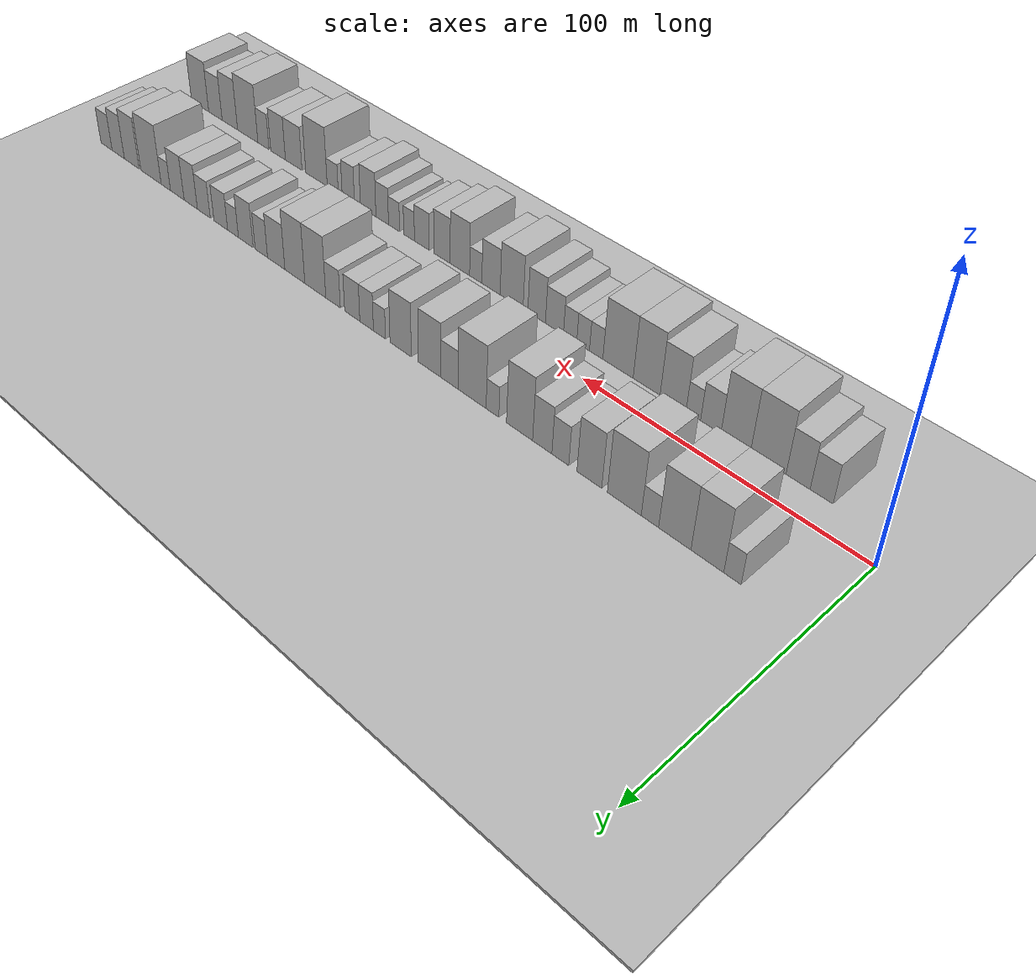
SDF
<?xml version="1.0" encoding="utf-8"?>

<sdf version="1.6">

   <world name="default">

      <gui fullscreen="0">

         <camera name="user_camera">

            <pose>-15 0 4.57585 0 0 0</pose>

            <view_controller>orbit</view_controller>

         </camera>

      </gui>

      <scene>

         <sky>

           <clouds>

             <speed>12</speed>

           </clouds>

         </sky>

         <ambient>0.4 0.4 0.4 1</ambient>

         <background>0.7 0.7 0.7 1</background>

         <shadows>1</shadows>

      </scene>

      <gravity>0 0 -9.8066</gravity>

      <magnetic_field>6e-06 2.3e-05 -4.2e-05</magnetic_field>

      <physics default="0" name="default_physics" type="ode">

         <ode>

            <solver>

               <type>quick</type>

               <iters>10</iters>

               <sor>1.0</sor>

               <use_dynamic_moi_rescaling>0</use_dynamic_moi_rescaling>

            </solver>

            <constraints>

               <cfm>0</cfm>

               <erp>0.2</erp>

               <contact_max_correcting_vel>100</contact_max_correcting_vel>

               <contact_surface_layer>0.001</contact_surface_layer>

            </constraints>

         </ode>

         <max_step_size>0.004</max_step_size>

         <real_time_factor>1</real_time_factor>

         <real_time_update_rate>250</real_time_update_rate>

      </physics>

      <light name="sun" type="directional">

         <cast_shadows>1</cast_shadows>

         <pose>0 0 10 0 0 0</pose>

         <diffuse>0.8 0.8 0.8 1</diffuse>

         <specular>0.2 0.2 0.2 1</specular>

         <attenuation>

            <range>1000</range>

            <constant>0.9</constant>

            <linear>0.01</linear>

            <quadratic>0.001</quadratic>

         </attenuation>

         <direction>-0.5 0.1 -0.9</direction>

      </light>

      <include>

         <name>ground_plane_1</name>

         <uri>model://HANNAS_ground_plane</uri>

         <pose>0 0 0  0 0 0</pose>

      </include>

      <include>

         <name>ground_plane_2</name>

         <uri>model://HANNAS_ground_plane</uri>

         <pose>100 0 0  0 0 0</pose>

      </include>

      <model name="building_1">

         <static>1</static>

         <pose frame="">22.7337 20.0000 0 0.000000 0.000000 1.570796</pose>

         <link name="link">

            <pose frame="">0 0 6.00 0 0 0</pose>

            <collision name="collision">

               <geometry>

                  <box>

                     <size>20.0000 5.4673 12.0000</size>

                  </box>

               </geometry>

               <max_contacts>10</max_contacts>

               <surface>

                  <contact>

                     <ode/>

                  </contact>

                  <bounce/>

                  <friction>

                     <torsional>

                        <ode/>

                     </torsional>

                     <ode/>

                  </friction>

               </surface>

            </collision>

            <visual name="visual">

               <cast_shadows>0</cast_shadows>

               <geometry>

                  <box>

                     <size>20.0000 5.4673 12.0000</size>

                  </box>

               </geometry>

               <material>

                  <script>

                     <uri>model://HANNAS_wall/materials/scripts</uri>

                     <uri>model://HANNAS_wall/materials/textures</uri>

                     <name>vrc/HANNAS_wall</name>

                  </script>

               </material>

            </visual>

            <self_collide>0</self_collide>

            <enable_wind>0</enable_wind>

            <kinematic>0</kinematic>

         </link>

      </model>

      <model name="building_2">

         <static>1</static>

         <pose frame="">30.7658 20.0000 0 0.000000 0.000000 1.570796</pose>

         <link name="link">

            <pose frame="">0 0 12.00 0 0 0</pose>

            <collision name="collision">

               <geometry>

                  <box>

                     <size>20.0000 10.5969 24.0000</size>

                  </box>

               </geometry>

               <max_contacts>10</max_contacts>

               <surface>

                  <contact>

                     <ode/>

                  </contact>

                  <bounce/>

                  <friction>

                     <torsional>

                        <ode/>

                     </torsional>

                     <ode/>

                  </friction>

               </surface>

            </collision>

            <visual name="visual">

               <cast_shadows>0</cast_shadows>

               <geometry>

                  <box>

                     <size>20.0000 10.5969 24.0000</size>

                  </box>

               </geometry>

               <material>

                  <script>

                     <uri>model://HANNAS_wall/materials/scripts</uri>

                     <uri>model://HANNAS_wall/materials/textures</uri>

                     <name>vrc/HANNAS_wall</name>

                  </script>

               </material>

            </visual>

            <self_collide>0</self_collide>

            <enable_wind>0</enable_wind>

            <kinematic>0</kinematic>

         </link>

      </model>

      <model name="building_3">

         <static>1</static>

         <pose frame="">41.4560 20.0000 0 0.000000 0.000000 1.570796</pose>

         <link name="link">

            <pose frame="">0 0 12.00 0 0 0</pose>

            <collision name="collision">

               <geometry>

                  <box>

                     <size>20.0000 10.7837 24.0000</size>

                  </box>

               </geometry>

               <max_contacts>10</max_contacts>

               <surface>

                  <contact>

                     <ode/>

                  </contact>

                  <bounce/>

                  <friction>

                     <torsional>

                        <ode/>

                     </torsional>

                     <ode/>

                  </friction>

               </surface>

            </collision>

            <visual name="visual">

               <cast_shadows>0</cast_shadows>

               <geometry>

                  <box>

                     <size>20.0000 10.7837 24.0000</size>

                  </box>

               </geometry>

               <material>

                  <script>

                     <uri>model://HANNAS_wall/materials/scripts</uri>

                     <uri>model://HANNAS_wall/materials/textures</uri>

                     <name>vrc/HANNAS_wall</name>

                  </script>

               </material>

            </visual>

            <self_collide>0</self_collide>

            <enable_wind>0</enable_wind>

            <kinematic>0</kinematic>

         </link>

      </model>

      <model name="building_4">

         <static>1</static>

         <pose frame="">49.8045 20.0000 0 0.000000 0.000000 1.570796</pose>

         <link name="link">

            <pose frame="">0 0 6.00 0 0 0</pose>

            <collision name="collision">

               <geometry>

                  <box>

                     <size>20.0000 5.9133 12.0000</size>

                  </box>

               </geometry>

               <max_contacts>10</max_contacts>

               <surface>

                  <contact>

                     <ode/>

                  </contact>

                  <bounce/>

                  <friction>

                     <torsional>

                        <ode/>

                     </torsional>

                     <ode/>

                  </friction>

               </surface>

            </collision>

            <visual name="visual">

               <cast_shadows>0</cast_shadows>

               <geometry>

                  <box>

                     <size>20.0000 5.9133 12.0000</size>

                  </box>

               </geometry>

               <material>

                  <script>

                     <uri>model://HANNAS_wall/materials/scripts</uri>

                     <uri>model://HANNAS_wall/materials/textures</uri>

                     <name>vrc/HANNAS_wall</name>

                  </script>

               </material>

            </visual>

            <self_collide>0</self_collide>

            <enable_wind>0</enable_wind>

            <kinematic>0</kinematic>

         </link>

      </model>

      <model name="building_5">

         <static>1</static>

         <pose frame="">58.6800 20.0000 0 0.000000 0.000000 1.570796</pose>

         <link name="link">

            <pose frame="">0 0 12.00 0 0 0</pose>

            <collision name="collision">

               <geometry>

                  <box>

                     <size>20.0000 11.8378 24.0000</size>

                  </box>

               </geometry>

               <max_contacts>10</max_contacts>

               <surface>

                  <contact>

                     <ode/>

                  </contact>

                  <bounce/>

                  <friction>

                     <torsional>

                        <ode/>

                     </torsional>

                     <ode/>

                  </friction>

               </surface>

            </collision>

            <visual name="visual">

               <cast_shadows>0</cast_shadows>

               <geometry>

                  <box>

                     <size>20.0000 11.8378 24.0000</size>

                  </box>

               </geometry>

               <material>

                  <script>

                     <uri>model://HANNAS_wall/materials/scripts</uri>

                     <uri>model://HANNAS_wall/materials/textures</uri>

                     <name>vrc/HANNAS_wall</name>

                  </script>

               </material>

            </visual>

            <self_collide>0</self_collide>

            <enable_wind>0</enable_wind>

            <kinematic>0</kinematic>

         </link>

      </model>

      <model name="building_6">

         <static>1</static>

         <pose frame="">71.0685 20.0000 0 0.000000 0.000000 1.570796</pose>

         <link name="link">

            <pose frame="">0 0 10.50 0 0 0</pose>

            <collision name="collision">

               <geometry>

                  <box>

                     <size>20.0000 8.9391 21.0000</size>

                  </box>

               </geometry>

               <max_contacts>10</max_contacts>

               <surface>

                  <contact>

                     <ode/>

                  </contact>

                  <bounce/>

                  <friction>

                     <torsional>

                        <ode/>

                     </torsional>

                     <ode/>

                  </friction>

               </surface>

            </collision>

            <visual name="visual">

               <cast_shadows>0</cast_shadows>

               <geometry>

                  <box>

                     <size>20.0000 8.9391 21.0000</size>

                  </box>

               </geometry>

               <material>

                  <script>

                     <uri>model://HANNAS_wall/materials/scripts</uri>

                     <uri>model://HANNAS_wall/materials/textures</uri>

                     <name>vrc/HANNAS_wall</name>

                  </script>

               </material>

            </visual>

            <self_collide>0</self_collide>

            <enable_wind>0</enable_wind>

            <kinematic>0</kinematic>

         </link>

      </model>

      <model name="building_7">

         <static>1</static>

         <pose frame="">81.6687 20.0000 0 0.000000 0.000000 1.570796</pose>

         <link name="link">

            <pose frame="">0 0 7.50 0 0 0</pose>

            <collision name="collision">

               <geometry>

                  <box>

                     <size>20.0000 6.2614 15.0000</size>

                  </box>

               </geometry>

               <max_contacts>10</max_contacts>

               <surface>

                  <contact>

                     <ode/>

                  </contact>

                  <bounce/>

                  <friction>

                     <torsional>

                        <ode/>

                     </torsional>

                     <ode/>

                  </friction>

               </surface>

            </collision>

            <visual name="visual">

               <cast_shadows>0</cast_shadows>

               <geometry>

                  <box>

                     <size>20.0000 6.2614 15.0000</size>

                  </box>

               </geometry>

               <material>

                  <script>

                     <uri>model://HANNAS_wall/materials/scripts</uri>

                     <uri>model://HANNAS_wall/materials/textures</uri>

                     <name>vrc/HANNAS_wall</name>

                  </script>

               </material>

            </visual>

            <self_collide>0</self_collide>

            <enable_wind>0</enable_wind>

            <kinematic>0</kinematic>

         </link>

      </model>

      <model name="building_8">

         <static>1</static>

         <pose frame="">88.4430 20.0000 0 0.000000 0.000000 1.570796</pose>

         <link name="link">

            <pose frame="">0 0 9.00 0 0 0</pose>

            <collision name="collision">

               <geometry>

                  <box>

                     <size>20.0000 7.2872 18.0000</size>

                  </box>

               </geometry>

               <max_contacts>10</max_contacts>

               <surface>

                  <contact>

                     <ode/>

                  </contact>

                  <bounce/>

                  <friction>

                     <torsional>

                        <ode/>

                     </torsional>

                     <ode/>

                  </friction>

               </surface>

            </collision>

            <visual name="visual">

               <cast_shadows>0</cast_shadows>

               <geometry>

                  <box>

                     <size>20.0000 7.2872 18.0000</size>

                  </box>

               </geometry>

               <material>

                  <script>

                     <uri>model://HANNAS_wall/materials/scripts</uri>

                     <uri>model://HANNAS_wall/materials/textures</uri>

                     <name>vrc/HANNAS_wall</name>

                  </script>

               </material>

            </visual>

            <self_collide>0</self_collide>

            <enable_wind>0</enable_wind>

            <kinematic>0</kinematic>

         </link>

      </model>

      <model name="building_9">

         <static>1</static>

         <pose frame="">97.1406 20.0000 0 0.000000 0.000000 1.570796</pose>

         <link name="link">

            <pose frame="">0 0 12.00 0 0 0</pose>

            <collision name="collision">

               <geometry>

                  <box>

                     <size>20.0000 10.1078 24.0000</size>

                  </box>

               </geometry>

               <max_contacts>10</max_contacts>

               <surface>

                  <contact>

                     <ode/>

                  </contact>

                  <bounce/>

                  <friction>

                     <torsional>

                        <ode/>

                     </torsional>

                     <ode/>

                  </friction>

               </surface>

            </collision>

            <visual name="visual">

               <cast_shadows>0</cast_shadows>

               <geometry>

                  <box>

                     <size>20.0000 10.1078 24.0000</size>

                  </box>

               </geometry>

               <material>

                  <script>

                     <uri>model://HANNAS_wall/materials/scripts</uri>

                     <uri>model://HANNAS_wall/materials/textures</uri>

                     <name>vrc/HANNAS_wall</name>

                  </script>

               </material>

            </visual>

            <self_collide>0</self_collide>

            <enable_wind>0</enable_wind>

            <kinematic>0</kinematic>

         </link>

      </model>

      <model name="building_10">

         <static>1</static>

         <pose frame="">107.7197 20.0000 0 0.000000 0.000000 1.570796</pose>

         <link name="link">

            <pose frame="">0 0 6.00 0 0 0</pose>

            <collision name="collision">

               <geometry>

                  <box>

                     <size>20.0000 5.0505 12.0000</size>

                  </box>

               </geometry>

               <max_contacts>10</max_contacts>

               <surface>

                  <contact>

                     <ode/>

                  </contact>

                  <bounce/>

                  <friction>

                     <torsional>

                        <ode/>

                     </torsional>

                     <ode/>

                  </friction>

               </surface>

            </collision>

            <visual name="visual">

               <cast_shadows>0</cast_shadows>

               <geometry>

                  <box>

                     <size>20.0000 5.0505 12.0000</size>

                  </box>

               </geometry>

               <material>

                  <script>

                     <uri>model://HANNAS_wall/materials/scripts</uri>

                     <uri>model://HANNAS_wall/materials/textures</uri>

                     <name>vrc/HANNAS_wall</name>

                  </script>

               </material>

            </visual>

            <self_collide>0</self_collide>

            <enable_wind>0</enable_wind>

            <kinematic>0</kinematic>

         </link>

      </model>

      <model name="building_11">

         <static>1</static>

         <pose frame="">115.9525 20.0000 0 0.000000 0.000000 1.570796</pose>

         <link name="link">

            <pose frame="">0 0 12.00 0 0 0</pose>

            <collision name="collision">

               <geometry>

                  <box>

                     <size>20.0000 11.4151 24.0000</size>

                  </box>

               </geometry>

               <max_contacts>10</max_contacts>

               <surface>

                  <contact>

                     <ode/>

                  </contact>

                  <bounce/>

                  <friction>

                     <torsional>

                        <ode/>

                     </torsional>

                     <ode/>

                  </friction>

               </surface>

            </collision>

            <visual name="visual">

               <cast_shadows>0</cast_shadows>

               <geometry>

                  <box>

                     <size>20.0000 11.4151 24.0000</size>

                  </box>

               </geometry>

               <material>

                  <script>

                     <uri>model://HANNAS_wall/materials/scripts</uri>

                     <uri>model://HANNAS_wall/materials/textures</uri>

                     <name>vrc/HANNAS_wall</name>

                  </script>

               </material>

            </visual>

            <self_collide>0</self_collide>

            <enable_wind>0</enable_wind>

            <kinematic>0</kinematic>

         </link>

      </model>

      <model name="building_12">

         <static>1</static>

         <pose frame="">125.2201 20.0000 0 0.000000 0.000000 1.570796</pose>

         <link name="link">

            <pose frame="">0 0 7.50 0 0 0</pose>

            <collision name="collision">

               <geometry>

                  <box>

                     <size>20.0000 7.1200 15.0000</size>

                  </box>

               </geometry>

               <max_contacts>10</max_contacts>

               <surface>

                  <contact>

                     <ode/>

                  </contact>

                  <bounce/>

                  <friction>

                     <torsional>

                        <ode/>

                     </torsional>

                     <ode/>

                  </friction>

               </surface>

            </collision>

            <visual name="visual">

               <cast_shadows>0</cast_shadows>

               <geometry>

                  <box>

                     <size>20.0000 7.1200 15.0000</size>

                  </box>

               </geometry>

               <material>

                  <script>

                     <uri>model://HANNAS_wall/materials/scripts</uri>

                     <uri>model://HANNAS_wall/materials/textures</uri>

                     <name>vrc/HANNAS_wall</name>

                  </script>

               </material>

            </visual>

            <self_collide>0</self_collide>

            <enable_wind>0</enable_wind>

            <kinematic>0</kinematic>

         </link>

      </model>

      <model name="building_13">

         <static>1</static>

         <pose frame="">133.5813 20.0000 0 0.000000 0.000000 1.570796</pose>

         <link name="link">

            <pose frame="">0 0 10.50 0 0 0</pose>

            <collision name="collision">

               <geometry>

                  <box>

                     <size>20.0000 9.6024 21.0000</size>

                  </box>

               </geometry>

               <max_contacts>10</max_contacts>

               <surface>

                  <contact>

                     <ode/>

                  </contact>

                  <bounce/>

                  <friction>

                     <torsional>

                        <ode/>

                     </torsional>

                     <ode/>

                  </friction>

               </surface>

            </collision>

            <visual name="visual">

               <cast_shadows>0</cast_shadows>

               <geometry>

                  <box>

                     <size>20.0000 9.6024 21.0000</size>

                  </box>

               </geometry>

               <material>

                  <script>

                     <uri>model://HANNAS_wall/materials/scripts</uri>

                     <uri>model://HANNAS_wall/materials/textures</uri>

                     <name>vrc/HANNAS_wall</name>

                  </script>

               </material>

            </visual>

            <self_collide>0</self_collide>

            <enable_wind>0</enable_wind>

            <kinematic>0</kinematic>

         </link>

      </model>

      <model name="building_14">

         <static>1</static>

         <pose frame="">146.0307 20.0000 0 0.000000 0.000000 1.570796</pose>

         <link name="link">

            <pose frame="">0 0 10.50 0 0 0</pose>

            <collision name="collision">

               <geometry>

                  <box>

                     <size>20.0000 9.2964 21.0000</size>

                  </box>

               </geometry>

               <max_contacts>10</max_contacts>

               <surface>

                  <contact>

                     <ode/>

                  </contact>

                  <bounce/>

                  <friction>

                     <torsional>

                        <ode/>

                     </torsional>

                     <ode/>

                  </friction>

               </surface>

            </collision>

            <visual name="visual">

               <cast_shadows>0</cast_shadows>

               <geometry>

                  <box>

                     <size>20.0000 9.2964 21.0000</size>

                  </box>

               </geometry>

               <material>

                  <script>

                     <uri>model://HANNAS_wall/materials/scripts</uri>

                     <uri>model://HANNAS_wall/materials/textures</uri>

                     <name>vrc/HANNAS_wall</name>

                  </script>

               </material>

            </visual>

            <self_collide>0</self_collide>

            <enable_wind>0</enable_wind>

            <kinematic>0</kinematic>

         </link>

      </model>

      <model name="building_15">

         <static>1</static>

         <pose frame="">155.3651 20.0000 0 0.000000 0.000000 1.570796</pose>

         <link name="link">

            <pose frame="">0 0 6.00 0 0 0</pose>

            <collision name="collision">

               <geometry>

                  <box>

                     <size>20.0000 5.3725 12.0000</size>

                  </box>

               </geometry>

               <max_contacts>10</max_contacts>

               <surface>

                  <contact>

                     <ode/>

                  </contact>

                  <bounce/>

                  <friction>

                     <torsional>

                        <ode/>

                     </torsional>

                     <ode/>

                  </friction>

               </surface>

            </collision>

            <visual name="visual">

               <cast_shadows>0</cast_shadows>

               <geometry>

                  <box>

                     <size>20.0000 5.3725 12.0000</size>

                  </box>

               </geometry>

               <material>

                  <script>

                     <uri>model://HANNAS_wall/materials/scripts</uri>

                     <uri>model://HANNAS_wall/materials/textures</uri>

                     <name>vrc/HANNAS_wall</name>

                  </script>

               </material>

            </visual>

            <self_collide>0</self_collide>

            <enable_wind>0</enable_wind>

            <kinematic>0</kinematic>

         </link>

      </model>

      <model name="building_16">

         <static>1</static>

         <pose frame="">161.1347 20.0000 0 0.000000 0.000000 1.570796</pose>

         <link name="link">

            <pose frame="">0 0 7.50 0 0 0</pose>

            <collision name="collision">

               <geometry>

                  <box>

                     <size>20.0000 6.1667 15.0000</size>

                  </box>

               </geometry>

               <max_contacts>10</max_contacts>

               <surface>

                  <contact>

                     <ode/>

                  </contact>

                  <bounce/>

                  <friction>

                     <torsional>

                        <ode/>

                     </torsional>

                     <ode/>

                  </friction>

               </surface>

            </collision>

            <visual name="visual">

               <cast_shadows>0</cast_shadows>

               <geometry>

                  <box>

                     <size>20.0000 6.1667 15.0000</size>

                  </box>

               </geometry>

               <material>

                  <script>

                     <uri>model://HANNAS_wall/materials/scripts</uri>

                     <uri>model://HANNAS_wall/materials/textures</uri>

                     <name>vrc/HANNAS_wall</name>

                  </script>

               </material>

            </visual>

            <self_collide>0</self_collide>

            <enable_wind>0</enable_wind>

            <kinematic>0</kinematic>

         </link>

      </model>

      <model name="building_17">

         <static>1</static>

         <pose frame="">167.7172 20.0000 0 0.000000 0.000000 1.570796</pose>

         <link name="link">

            <pose frame="">0 0 7.50 0 0 0</pose>

            <collision name="collision">

               <geometry>

                  <box>

                     <size>20.0000 6.9982 15.0000</size>

                  </box>

               </geometry>

               <max_contacts>10</max_contacts>

               <surface>

                  <contact>

                     <ode/>

                  </contact>

                  <bounce/>

                  <friction>

                     <torsional>

                        <ode/>

                     </torsional>

                     <ode/>

                  </friction>

               </surface>

            </collision>

            <visual name="visual">

               <cast_shadows>0</cast_shadows>

               <geometry>

                  <box>

                     <size>20.0000 6.9982 15.0000</size>

                  </box>

               </geometry>

               <material>

                  <script>

                     <uri>model://HANNAS_wall/materials/scripts</uri>

                     <uri>model://HANNAS_wall/materials/textures</uri>

                     <name>vrc/HANNAS_wall</name>

                  </script>

               </material>

            </visual>

            <self_collide>0</self_collide>

            <enable_wind>0</enable_wind>

            <kinematic>0</kinematic>

         </link>

      </model>

      <model name="building_18">

         <static>1</static>

         <pose frame="">176.6432 20.0000 0 0.000000 0.000000 1.570796</pose>

         <link name="link">

            <pose frame="">0 0 7.50 0 0 0</pose>

            <collision name="collision">

               <geometry>

                  <box>

                     <size>20.0000 6.8539 15.0000</size>

                  </box>

               </geometry>

               <max_contacts>10</max_contacts>

               <surface>

                  <contact>

                     <ode/>

                  </contact>

                  <bounce/>

                  <friction>

                     <torsional>

                        <ode/>

                     </torsional>

                     <ode/>

                  </friction>

               </surface>

            </collision>

            <visual name="visual">

               <cast_shadows>0</cast_shadows>

               <geometry>

                  <box>

                     <size>20.0000 6.8539 15.0000</size>

                  </box>

               </geometry>

               <material>

                  <script>

                     <uri>model://HANNAS_wall/materials/scripts</uri>

                     <uri>model://HANNAS_wall/materials/textures</uri>

                     <name>vrc/HANNAS_wall</name>

                  </script>

               </material>

            </visual>

            <self_collide>0</self_collide>

            <enable_wind>0</enable_wind>

            <kinematic>0</kinematic>

         </link>

      </model>

      <model name="building_19">

         <static>1</static>

         <pose frame="">185.0944 20.0000 0 0.000000 0.000000 1.570796</pose>

         <link name="link">

            <pose frame="">0 0 12.00 0 0 0</pose>

            <collision name="collision">

               <geometry>

                  <box>

                     <size>20.0000 10.0486 24.0000</size>

                  </box>

               </geometry>

               <max_contacts>10</max_contacts>

               <surface>

                  <contact>

                     <ode/>

                  </contact>

                  <bounce/>

                  <friction>

                     <torsional>

                        <ode/>

                     </torsional>

                     <ode/>

                  </friction>

               </surface>

            </collision>

            <visual name="visual">

               <cast_shadows>0</cast_shadows>

               <geometry>

                  <box>

                     <size>20.0000 10.0486 24.0000</size>

                  </box>

               </geometry>

               <material>

                  <script>

                     <uri>model://HANNAS_wall/materials/scripts</uri>

                     <uri>model://HANNAS_wall/materials/textures</uri>

                     <name>vrc/HANNAS_wall</name>

                  </script>

               </material>

            </visual>

            <self_collide>0</self_collide>

            <enable_wind>0</enable_wind>

            <kinematic>0</kinematic>

         </link>

      </model>

      <model name="building_20">

         <static>1</static>

         <pose frame="">195.0216 20.0000 0 0.000000 0.000000 1.570796</pose>

         <link name="link">

            <pose frame="">0 0 12.00 0 0 0</pose>

            <collision name="collision">

               <geometry>

                  <box>

                     <size>20.0000 9.8058 24.0000</size>

                  </box>

               </geometry>

               <max_contacts>10</max_contacts>

               <surface>

                  <contact>

                     <ode/>

                  </contact>

                  <bounce/>

                  <friction>

                     <torsional>

                        <ode/>

                     </torsional>

                     <ode/>

                  </friction>

               </surface>

            </collision>

            <visual name="visual">

               <cast_shadows>0</cast_shadows>

               <geometry>

                  <box>

                     <size>20.0000 9.8058 24.0000</size>

                  </box>

               </geometry>

               <material>

                  <script>

                     <uri>model://HANNAS_wall/materials/scripts</uri>

                     <uri>model://HANNAS_wall/materials/textures</uri>

                     <name>vrc/HANNAS_wall</name>

                  </script>

               </material>

            </visual>

            <self_collide>0</self_collide>

            <enable_wind>0</enable_wind>

            <kinematic>0</kinematic>

         </link>

      </model>

      <model name="building_21">

         <static>1</static>

         <pose frame="">204.2765 20.0000 0 0.000000 0.000000 1.570796</pose>

         <link name="link">

            <pose frame="">0 0 9.00 0 0 0</pose>

            <collision name="collision">

               <geometry>

                  <box>

                     <size>20.0000 8.7040 18.0000</size>

                  </box>

               </geometry>

               <max_contacts>10</max_contacts>

               <surface>

                  <contact>

                     <ode/>

                  </contact>

                  <bounce/>

                  <friction>

                     <torsional>

                        <ode/>

                     </torsional>

                     <ode/>

                  </friction>

               </surface>

            </collision>

            <visual name="visual">

               <cast_shadows>0</cast_shadows>

               <geometry>

                  <box>

                     <size>20.0000 8.7040 18.0000</size>

                  </box>

               </geometry>

               <material>

                  <script>

                     <uri>model://HANNAS_wall/materials/scripts</uri>

                     <uri>model://HANNAS_wall/materials/textures</uri>

                     <name>vrc/HANNAS_wall</name>

                  </script>

               </material>

            </visual>

            <self_collide>0</self_collide>

            <enable_wind>0</enable_wind>

            <kinematic>0</kinematic>

         </link>

      </model>

      <model name="building_22">

         <static>1</static>

         <pose frame="">211.7917 20.0000 0 0.000000 0.000000 1.570796</pose>

         <link name="link">

            <pose frame="">0 0 7.50 0 0 0</pose>

            <collision name="collision">

               <geometry>

                  <box>

                     <size>20.0000 6.3265 15.0000</size>

                  </box>

               </geometry>

               <max_contacts>10</max_contacts>

               <surface>

                  <contact>

                     <ode/>

                  </contact>

                  <bounce/>

                  <friction>

                     <torsional>

                        <ode/>

                     </torsional>

                     <ode/>

                  </friction>

               </surface>

            </collision>

            <visual name="visual">

               <cast_shadows>0</cast_shadows>

               <geometry>

                  <box>

                     <size>20.0000 6.3265 15.0000</size>

                  </box>

               </geometry>

               <material>

                  <script>

                     <uri>model://HANNAS_wall/materials/scripts</uri>

                     <uri>model://HANNAS_wall/materials/textures</uri>

                     <name>vrc/HANNAS_wall</name>

                  </script>

               </material>

            </visual>

            <self_collide>0</self_collide>

            <enable_wind>0</enable_wind>

            <kinematic>0</kinematic>

         </link>

      </model>

      <model name="building_23">

         <static>1</static>

         <pose frame="">219.7814 20.0000 0 0.000000 0.000000 1.570796</pose>

         <link name="link">

            <pose frame="">0 0 9.00 0 0 0</pose>

            <collision name="collision">

               <geometry>

                  <box>

                     <size>20.0000 7.6528 18.0000</size>

                  </box>

               </geometry>

               <max_contacts>10</max_contacts>

               <surface>

                  <contact>

                     <ode/>

                  </contact>

                  <bounce/>

                  <friction>

                     <torsional>

                        <ode/>

                     </torsional>

                     <ode/>

                  </friction>

               </surface>

            </collision>

            <visual name="visual">

               <cast_shadows>0</cast_shadows>

               <geometry>

                  <box>

                     <size>20.0000 7.6528 18.0000</size>

                  </box>

               </geometry>

               <material>

                  <script>

                     <uri>model://HANNAS_wall/materials/scripts</uri>

                     <uri>model://HANNAS_wall/materials/textures</uri>

                     <name>vrc/HANNAS_wall</name>

                  </script>

               </material>

            </visual>

            <self_collide>0</self_collide>

            <enable_wind>0</enable_wind>

            <kinematic>0</kinematic>

         </link>

      </model>

      <model name="building_24">

         <static>1</static>

         <pose frame="">226.4473 20.0000 0 0.000000 0.000000 1.570796</pose>

         <link name="link">

            <pose frame="">0 0 6.00 0 0 0</pose>

            <collision name="collision">

               <geometry>

                  <box>

                     <size>20.0000 5.6790 12.0000</size>

                  </box>

               </geometry>

               <max_contacts>10</max_contacts>

               <surface>

                  <contact>

                     <ode/>

                  </contact>

                  <bounce/>

                  <friction>

                     <torsional>

                        <ode/>

                     </torsional>

                     <ode/>

                  </friction>

               </surface>

            </collision>

            <visual name="visual">

               <cast_shadows>0</cast_shadows>

               <geometry>

                  <box>

                     <size>20.0000 5.6790 12.0000</size>

                  </box>

               </geometry>

               <material>

                  <script>

                     <uri>model://HANNAS_wall/materials/scripts</uri>

                     <uri>model://HANNAS_wall/materials/textures</uri>

                     <name>vrc/HANNAS_wall</name>

                  </script>

               </material>

            </visual>

            <self_collide>0</self_collide>

            <enable_wind>0</enable_wind>

            <kinematic>0</kinematic>

         </link>

      </model>

      <model name="building_25">

         <static>1</static>

         <pose frame="">232.9609 20.0000 0 0.000000 0.000000 1.570796</pose>

         <link name="link">

            <pose frame="">0 0 7.50 0 0 0</pose>

            <collision name="collision">

               <geometry>

                  <box>

                     <size>20.0000 7.3481 15.0000</size>

                  </box>

               </geometry>

               <max_contacts>10</max_contacts>

               <surface>

                  <contact>

                     <ode/>

                  </contact>

                  <bounce/>

                  <friction>

                     <torsional>

                        <ode/>

                     </torsional>

                     <ode/>

                  </friction>

               </surface>

            </collision>

            <visual name="visual">

               <cast_shadows>0</cast_shadows>

               <geometry>

                  <box>

                     <size>20.0000 7.3481 15.0000</size>

                  </box>

               </geometry>

               <material>

                  <script>

                     <uri>model://HANNAS_wall/materials/scripts</uri>

                     <uri>model://HANNAS_wall/materials/textures</uri>

                     <name>vrc/HANNAS_wall</name>

                  </script>

               </material>

            </visual>

            <self_collide>0</self_collide>

            <enable_wind>0</enable_wind>

            <kinematic>0</kinematic>

         </link>

      </model>

      <model name="building_26">

         <static>1</static>

         <pose frame="">242.1310 20.0000 0 0.000000 0.000000 1.570796</pose>

         <link name="link">

            <pose frame="">0 0 7.50 0 0 0</pose>

            <collision name="collision">

               <geometry>

                  <box>

                     <size>20.0000 6.9921 15.0000</size>

                  </box>

               </geometry>

               <max_contacts>10</max_contacts>

               <surface>

                  <contact>

                     <ode/>

                  </contact>

                  <bounce/>

                  <friction>

                     <torsional>

                        <ode/>

                     </torsional>

                     <ode/>

                  </friction>

               </surface>

            </collision>

            <visual name="visual">

               <cast_shadows>0</cast_shadows>

               <geometry>

                  <box>

                     <size>20.0000 6.9921 15.0000</size>

                  </box>

               </geometry>

               <material>

                  <script>

                     <uri>model://HANNAS_wall/materials/scripts</uri>

                     <uri>model://HANNAS_wall/materials/textures</uri>

                     <name>vrc/HANNAS_wall</name>

                  </script>

               </material>

            </visual>

            <self_collide>0</self_collide>

            <enable_wind>0</enable_wind>

            <kinematic>0</kinematic>

         </link>

      </model>

      <model name="building_27">

         <static>1</static>

         <pose frame="">249.3128 20.0000 0 0.000000 0.000000 1.570796</pose>

         <link name="link">

            <pose frame="">0 0 9.00 0 0 0</pose>

            <collision name="collision">

               <geometry>

                  <box>

                     <size>20.0000 7.3713 18.0000</size>

                  </box>

               </geometry>

               <max_contacts>10</max_contacts>

               <surface>

                  <contact>

                     <ode/>

                  </contact>

                  <bounce/>

                  <friction>

                     <torsional>

                        <ode/>

                     </torsional>

                     <ode/>

                  </friction>

               </surface>

            </collision>

            <visual name="visual">

               <cast_shadows>0</cast_shadows>

               <geometry>

                  <box>

                     <size>20.0000 7.3713 18.0000</size>

                  </box>

               </geometry>

               <material>

                  <script>

                     <uri>model://HANNAS_wall/materials/scripts</uri>

                     <uri>model://HANNAS_wall/materials/textures</uri>

                     <name>vrc/HANNAS_wall</name>

                  </script>

               </material>

            </visual>

            <self_collide>0</self_collide>

            <enable_wind>0</enable_wind>

            <kinematic>0</kinematic>

         </link>

      </model>

      <model name="building_28">

         <static>1</static>

         <pose frame="">256.8416 20.0000 0 0.000000 0.000000 1.570796</pose>

         <link name="link">

            <pose frame="">0 0 9.00 0 0 0</pose>

            <collision name="collision">

               <geometry>

                  <box>

                     <size>20.0000 7.6865 18.0000</size>

                  </box>

               </geometry>

               <max_contacts>10</max_contacts>

               <surface>

                  <contact>

                     <ode/>

                  </contact>

                  <bounce/>

                  <friction>

                     <torsional>

                        <ode/>

                     </torsional>

                     <ode/>

                  </friction>

               </surface>

            </collision>

            <visual name="visual">

               <cast_shadows>0</cast_shadows>

               <geometry>

                  <box>

                     <size>20.0000 7.6865 18.0000</size>

                  </box>

               </geometry>

               <material>

                  <script>

                     <uri>model://HANNAS_wall/materials/scripts</uri>

                     <uri>model://HANNAS_wall/materials/textures</uri>

                     <name>vrc/HANNAS_wall</name>

                  </script>

               </material>

            </visual>

            <self_collide>0</self_collide>

            <enable_wind>0</enable_wind>

            <kinematic>0</kinematic>

         </link>

      </model>

      <model name="building_29">

         <static>1</static>

         <pose frame="">263.3319 20.0000 0 0.000000 0.000000 1.570796</pose>

         <link name="link">

            <pose frame="">0 0 6.00 0 0 0</pose>

            <collision name="collision">

               <geometry>

                  <box>

                     <size>20.0000 5.2941 12.0000</size>

                  </box>

               </geometry>

               <max_contacts>10</max_contacts>

               <surface>

                  <contact>

                     <ode/>

                  </contact>

                  <bounce/>

                  <friction>

                     <torsional>

                        <ode/>

                     </torsional>

                     <ode/>

                  </friction>

               </surface>

            </collision>

            <visual name="visual">

               <cast_shadows>0</cast_shadows>

               <geometry>

                  <box>

                     <size>20.0000 5.2941 12.0000</size>

                  </box>

               </geometry>

               <material>

                  <script>

                     <uri>model://HANNAS_wall/materials/scripts</uri>

                     <uri>model://HANNAS_wall/materials/textures</uri>

                     <name>vrc/HANNAS_wall</name>

                  </script>

               </material>

            </visual>

            <self_collide>0</self_collide>

            <enable_wind>0</enable_wind>

            <kinematic>0</kinematic>

         </link>

      </model>

      <model name="building_30">

         <static>1</static>

         <pose frame="">271.9318 20.0000 0 0.000000 0.000000 1.570796</pose>

         <link name="link">

            <pose frame="">0 0 12.00 0 0 0</pose>

            <collision name="collision">

               <geometry>

                  <box>

                     <size>20.0000 11.9057 24.0000</size>

                  </box>

               </geometry>

               <max_contacts>10</max_contacts>

               <surface>

                  <contact>

                     <ode/>

                  </contact>

                  <bounce/>

                  <friction>

                     <torsional>

                        <ode/>

                     </torsional>

                     <ode/>

                  </friction>

               </surface>

            </collision>

            <visual name="visual">

               <cast_shadows>0</cast_shadows>

               <geometry>

                  <box>

                     <size>20.0000 11.9057 24.0000</size>

                  </box>

               </geometry>

               <material>

                  <script>

                     <uri>model://HANNAS_wall/materials/scripts</uri>

                     <uri>model://HANNAS_wall/materials/textures</uri>

                     <name>vrc/HANNAS_wall</name>

                  </script>

               </material>

            </visual>

            <self_collide>0</self_collide>

            <enable_wind>0</enable_wind>

            <kinematic>0</kinematic>

         </link>

      </model>

      <model name="building_31">

         <static>1</static>

         <pose frame="">283.2652 20.0000 0 0.000000 0.000000 1.570796</pose>

         <link name="link">

            <pose frame="">0 0 10.50 0 0 0</pose>

            <collision name="collision">

               <geometry>

                  <box>

                     <size>20.0000 8.7612 21.0000</size>

                  </box>

               </geometry>

               <max_contacts>10</max_contacts>

               <surface>

                  <contact>

                     <ode/>

                  </contact>

                  <bounce/>

                  <friction>

                     <torsional>

                        <ode/>

                     </torsional>

                     <ode/>

                  </friction>

               </surface>

            </collision>

            <visual name="visual">

               <cast_shadows>0</cast_shadows>

               <geometry>

                  <box>

                     <size>20.0000 8.7612 21.0000</size>

                  </box>

               </geometry>

               <material>

                  <script>

                     <uri>model://HANNAS_wall/materials/scripts</uri>

                     <uri>model://HANNAS_wall/materials/textures</uri>

                     <name>vrc/HANNAS_wall</name>

                  </script>

               </material>

            </visual>

            <self_collide>0</self_collide>

            <enable_wind>0</enable_wind>

            <kinematic>0</kinematic>

         </link>

      </model>

      <model name="building_32">

         <static>1</static>

         <pose frame="">291.3849 20.0000 0 0.000000 0.000000 1.570796</pose>

         <link name="link">

            <pose frame="">0 0 9.00 0 0 0</pose>

            <collision name="collision">

               <geometry>

                  <box>

                     <size>20.0000 7.4781 18.0000</size>

                  </box>

               </geometry>

               <max_contacts>10</max_contacts>

               <surface>

                  <contact>

                     <ode/>

                  </contact>

                  <bounce/>

                  <friction>

                     <torsional>

                        <ode/>

                     </torsional>

                     <ode/>

                  </friction>

               </surface>

            </collision>

            <visual name="visual">

               <cast_shadows>0</cast_shadows>

               <geometry>

                  <box>

                     <size>20.0000 7.4781 18.0000</size>

                  </box>

               </geometry>

               <material>

                  <script>

                     <uri>model://HANNAS_wall/materials/scripts</uri>

                     <uri>model://HANNAS_wall/materials/textures</uri>

                     <name>vrc/HANNAS_wall</name>

                  </script>

               </material>

            </visual>

            <self_collide>0</self_collide>

            <enable_wind>0</enable_wind>

            <kinematic>0</kinematic>

         </link>

      </model>

      <model name="building_33">

         <static>1</static>

         <pose frame="">298.5321 20.0000 0 0.000000 0.000000 1.570796</pose>

         <link name="link">

            <pose frame="">0 0 7.50 0 0 0</pose>

            <collision name="collision">

               <geometry>

                  <box>

                     <size>20.0000 6.8162 15.0000</size>

                  </box>

               </geometry>

               <max_contacts>10</max_contacts>

               <surface>

                  <contact>

                     <ode/>

                  </contact>

                  <bounce/>

                  <friction>

                     <torsional>

                        <ode/>

                     </torsional>

                     <ode/>

                  </friction>

               </surface>

            </collision>

            <visual name="visual">

               <cast_shadows>0</cast_shadows>

               <geometry>

                  <box>

                     <size>20.0000 6.8162 15.0000</size>

                  </box>

               </geometry>

               <material>

                  <script>

                     <uri>model://HANNAS_wall/materials/scripts</uri>

                     <uri>model://HANNAS_wall/materials/textures</uri>

                     <name>vrc/HANNAS_wall</name>

                  </script>

               </material>

            </visual>

            <self_collide>0</self_collide>

            <enable_wind>0</enable_wind>

            <kinematic>0</kinematic>

         </link>

      </model>

      <model name="building_34">

         <static>1</static>

         <pose frame="">23.6889 -20.0000 0 0.000000 0.000000 1.570796</pose>

         <link name="link">

            <pose frame="">0 0 7.50 0 0 0</pose>

            <collision name="collision">

               <geometry>

                  <box>

                     <size>20.0000 7.3778 15.0000</size>

                  </box>

               </geometry>

               <max_contacts>10</max_contacts>

               <surface>

                  <contact>

                     <ode/>

                  </contact>

                  <bounce/>

                  <friction>

                     <torsional>

                        <ode/>

                     </torsional>

                     <ode/>

                  </friction>

               </surface>

            </collision>

            <visual name="visual">

               <cast_shadows>0</cast_shadows>

               <geometry>

                  <box>

                     <size>20.0000 7.3778 15.0000</size>

                  </box>

               </geometry>

               <material>

                  <script>

                     <uri>model://HANNAS_wall/materials/scripts</uri>

                     <uri>model://HANNAS_wall/materials/textures</uri>

                     <name>vrc/HANNAS_wall</name>

                  </script>

               </material>

            </visual>

            <self_collide>0</self_collide>

            <enable_wind>0</enable_wind>

            <kinematic>0</kinematic>

         </link>

      </model>

      <model name="building_35">

         <static>1</static>

         <pose frame="">31.3292 -20.0000 0 0.000000 0.000000 1.570796</pose>

         <link name="link">

            <pose frame="">0 0 9.00 0 0 0</pose>

            <collision name="collision">

               <geometry>

                  <box>

                     <size>20.0000 7.9028 18.0000</size>

                  </box>

               </geometry>

               <max_contacts>10</max_contacts>

               <surface>

                  <contact>

                     <ode/>

                  </contact>

                  <bounce/>

                  <friction>

                     <torsional>

                        <ode/>

                     </torsional>

                     <ode/>

                  </friction>

               </surface>

            </collision>

            <visual name="visual">

               <cast_shadows>0</cast_shadows>

               <geometry>

                  <box>

                     <size>20.0000 7.9028 18.0000</size>

                  </box>

               </geometry>

               <material>

                  <script>

                     <uri>model://HANNAS_wall/materials/scripts</uri>

                     <uri>model://HANNAS_wall/materials/textures</uri>

                     <name>vrc/HANNAS_wall</name>

                  </script>

               </material>

            </visual>

            <self_collide>0</self_collide>

            <enable_wind>0</enable_wind>

            <kinematic>0</kinematic>

         </link>

      </model>

      <model name="building_36">

         <static>1</static>

         <pose frame="">41.2298 -20.0000 0 0.000000 0.000000 1.570796</pose>

         <link name="link">

            <pose frame="">0 0 12.00 0 0 0</pose>

            <collision name="collision">

               <geometry>

                  <box>

                     <size>20.0000 11.8984 24.0000</size>

                  </box>

               </geometry>

               <max_contacts>10</max_contacts>

               <surface>

                  <contact>

                     <ode/>

                  </contact>

                  <bounce/>

                  <friction>

                     <torsional>

                        <ode/>

                     </torsional>

                     <ode/>

                  </friction>

               </surface>

            </collision>

            <visual name="visual">

               <cast_shadows>0</cast_shadows>

               <geometry>

                  <box>

                     <size>20.0000 11.8984 24.0000</size>

                  </box>

               </geometry>

               <material>

                  <script>

                     <uri>model://HANNAS_wall/materials/scripts</uri>

                     <uri>model://HANNAS_wall/materials/textures</uri>

                     <name>vrc/HANNAS_wall</name>

                  </script>

               </material>

            </visual>

            <self_collide>0</self_collide>

            <enable_wind>0</enable_wind>

            <kinematic>0</kinematic>

         </link>

      </model>

      <model name="building_37">

         <static>1</static>

         <pose frame="">52.3136 -20.0000 0 0.000000 0.000000 1.570796</pose>

         <link name="link">

            <pose frame="">0 0 12.00 0 0 0</pose>

            <collision name="collision">

               <geometry>

                  <box>

                     <size>20.0000 10.2692 24.0000</size>

                  </box>

               </geometry>

               <max_contacts>10</max_contacts>

               <surface>

                  <contact>

                     <ode/>

                  </contact>

                  <bounce/>

                  <friction>

                     <torsional>

                        <ode/>

                     </torsional>

                     <ode/>

                  </friction>

               </surface>

            </collision>

            <visual name="visual">

               <cast_shadows>0</cast_shadows>

               <geometry>

                  <box>

                     <size>20.0000 10.2692 24.0000</size>

                  </box>

               </geometry>

               <material>

                  <script>

                     <uri>model://HANNAS_wall/materials/scripts</uri>

                     <uri>model://HANNAS_wall/materials/textures</uri>

                     <name>vrc/HANNAS_wall</name>

                  </script>

               </material>

            </visual>

            <self_collide>0</self_collide>

            <enable_wind>0</enable_wind>

            <kinematic>0</kinematic>

         </link>

      </model>

      <model name="building_38">

         <static>1</static>

         <pose frame="">61.0539 -20.0000 0 0.000000 0.000000 1.570796</pose>

         <link name="link">

            <pose frame="">0 0 7.50 0 0 0</pose>

            <collision name="collision">

               <geometry>

                  <box>

                     <size>20.0000 7.2115 15.0000</size>

                  </box>

               </geometry>

               <max_contacts>10</max_contacts>

               <surface>

                  <contact>

                     <ode/>

                  </contact>

                  <bounce/>

                  <friction>

                     <torsional>

                        <ode/>

                     </torsional>

                     <ode/>

                  </friction>

               </surface>

            </collision>

            <visual name="visual">

               <cast_shadows>0</cast_shadows>

               <geometry>

                  <box>

                     <size>20.0000 7.2115 15.0000</size>

                  </box>

               </geometry>

               <material>

                  <script>

                     <uri>model://HANNAS_wall/materials/scripts</uri>

                     <uri>model://HANNAS_wall/materials/textures</uri>

                     <name>vrc/HANNAS_wall</name>

                  </script>

               </material>

            </visual>

            <self_collide>0</self_collide>

            <enable_wind>0</enable_wind>

            <kinematic>0</kinematic>

         </link>

      </model>

      <model name="building_39">

         <static>1</static>

         <pose frame="">67.2679 -20.0000 0 0.000000 0.000000 1.570796</pose>

         <link name="link">

            <pose frame="">0 0 6.00 0 0 0</pose>

            <collision name="collision">

               <geometry>

                  <box>

                     <size>20.0000 5.2165 12.0000</size>

                  </box>

               </geometry>

               <max_contacts>10</max_contacts>

               <surface>

                  <contact>

                     <ode/>

                  </contact>

                  <bounce/>

                  <friction>

                     <torsional>

                        <ode/>

                     </torsional>

                     <ode/>

                  </friction>

               </surface>

            </collision>

            <visual name="visual">

               <cast_shadows>0</cast_shadows>

               <geometry>

                  <box>

                     <size>20.0000 5.2165 12.0000</size>

                  </box>

               </geometry>

               <material>

                  <script>

                     <uri>model://HANNAS_wall/materials/scripts</uri>

                     <uri>model://HANNAS_wall/materials/textures</uri>

                     <name>vrc/HANNAS_wall</name>

                  </script>

               </material>

            </visual>

            <self_collide>0</self_collide>

            <enable_wind>0</enable_wind>

            <kinematic>0</kinematic>

         </link>

      </model>

      <model name="building_40">

         <static>1</static>

         <pose frame="">74.6307 -20.0000 0 0.000000 0.000000 1.570796</pose>

         <link name="link">

            <pose frame="">0 0 10.50 0 0 0</pose>

            <collision name="collision">

               <geometry>

                  <box>

                     <size>20.0000 9.5090 21.0000</size>

                  </box>

               </geometry>

               <max_contacts>10</max_contacts>

               <surface>

                  <contact>

                     <ode/>

                  </contact>

                  <bounce/>

                  <friction>

                     <torsional>

                        <ode/>

                     </torsional>

                     <ode/>

                  </friction>

               </surface>

            </collision>

            <visual name="visual">

               <cast_shadows>0</cast_shadows>

               <geometry>

                  <box>

                     <size>20.0000 9.5090 21.0000</size>

                  </box>

               </geometry>

               <material>

                  <script>

                     <uri>model://HANNAS_wall/materials/scripts</uri>

                     <uri>model://HANNAS_wall/materials/textures</uri>

                     <name>vrc/HANNAS_wall</name>

                  </script>

               </material>

            </visual>

            <self_collide>0</self_collide>

            <enable_wind>0</enable_wind>

            <kinematic>0</kinematic>

         </link>

      </model>

      <model name="building_41">

         <static>1</static>

         <pose frame="">84.4495 -20.0000 0 0.000000 0.000000 1.570796</pose>

         <link name="link">

            <pose frame="">0 0 12.00 0 0 0</pose>

            <collision name="collision">

               <geometry>

                  <box>

                     <size>20.0000 10.1286 24.0000</size>

                  </box>

               </geometry>

               <max_contacts>10</max_contacts>

               <surface>

                  <contact>

                     <ode/>

                  </contact>

                  <bounce/>

                  <friction>

                     <torsional>

                        <ode/>

                     </torsional>

                     <ode/>

                  </friction>

               </surface>

            </collision>

            <visual name="visual">

               <cast_shadows>0</cast_shadows>

               <geometry>

                  <box>

                     <size>20.0000 10.1286 24.0000</size>

                  </box>

               </geometry>

               <material>

                  <script>

                     <uri>model://HANNAS_wall/materials/scripts</uri>

                     <uri>model://HANNAS_wall/materials/textures</uri>

                     <name>vrc/HANNAS_wall</name>

                  </script>

               </material>

            </visual>

            <self_collide>0</self_collide>

            <enable_wind>0</enable_wind>

            <kinematic>0</kinematic>

         </link>

      </model>

      <model name="building_42">

         <static>1</static>

         <pose frame="">95.3755 -20.0000 0 0.000000 0.000000 1.570796</pose>

         <link name="link">

            <pose frame="">0 0 12.00 0 0 0</pose>

            <collision name="collision">

               <geometry>

                  <box>

                     <size>20.0000 11.7234 24.0000</size>

                  </box>

               </geometry>

               <max_contacts>10</max_contacts>

               <surface>

                  <contact>

                     <ode/>

                  </contact>

                  <bounce/>

                  <friction>

                     <torsional>

                        <ode/>

                     </torsional>

                     <ode/>

                  </friction>

               </surface>

            </collision>

            <visual name="visual">

               <cast_shadows>0</cast_shadows>

               <geometry>

                  <box>

                     <size>20.0000 11.7234 24.0000</size>

                  </box>

               </geometry>

               <material>

                  <script>

                     <uri>model://HANNAS_wall/materials/scripts</uri>

                     <uri>model://HANNAS_wall/materials/textures</uri>

                     <name>vrc/HANNAS_wall</name>

                  </script>

               </material>

            </visual>

            <self_collide>0</self_collide>

            <enable_wind>0</enable_wind>

            <kinematic>0</kinematic>

         </link>

      </model>

      <model name="building_43">

         <static>1</static>

         <pose frame="">103.8726 -20.0000 0 0.000000 0.000000 1.570796</pose>

         <link name="link">

            <pose frame="">0 0 6.00 0 0 0</pose>

            <collision name="collision">

               <geometry>

                  <box>

                     <size>20.0000 5.2709 12.0000</size>

                  </box>

               </geometry>

               <max_contacts>10</max_contacts>

               <surface>

                  <contact>

                     <ode/>

                  </contact>

                  <bounce/>

                  <friction>

                     <torsional>

                        <ode/>

                     </torsional>

                     <ode/>

                  </friction>

               </surface>

            </collision>

            <visual name="visual">

               <cast_shadows>0</cast_shadows>

               <geometry>

                  <box>

                     <size>20.0000 5.2709 12.0000</size>

                  </box>

               </geometry>

               <material>

                  <script>

                     <uri>model://HANNAS_wall/materials/scripts</uri>

                     <uri>model://HANNAS_wall/materials/textures</uri>

                     <name>vrc/HANNAS_wall</name>

                  </script>

               </material>

            </visual>

            <self_collide>0</self_collide>

            <enable_wind>0</enable_wind>

            <kinematic>0</kinematic>

         </link>

      </model>

      <model name="building_44">

         <static>1</static>

         <pose frame="">109.0506 -20.0000 0 0.000000 0.000000 1.570796</pose>

         <link name="link">

            <pose frame="">0 0 6.00 0 0 0</pose>

            <collision name="collision">

               <geometry>

                  <box>

                     <size>20.0000 5.0851 12.0000</size>

                  </box>

               </geometry>

               <max_contacts>10</max_contacts>

               <surface>

                  <contact>

                     <ode/>

                  </contact>

                  <bounce/>

                  <friction>

                     <torsional>

                        <ode/>

                     </torsional>

                     <ode/>

                  </friction>

               </surface>

            </collision>

            <visual name="visual">

               <cast_shadows>0</cast_shadows>

               <geometry>

                  <box>

                     <size>20.0000 5.0851 12.0000</size>

                  </box>

               </geometry>

               <material>

                  <script>

                     <uri>model://HANNAS_wall/materials/scripts</uri>

                     <uri>model://HANNAS_wall/materials/textures</uri>

                     <name>vrc/HANNAS_wall</name>

                  </script>

               </material>

            </visual>

            <self_collide>0</self_collide>

            <enable_wind>0</enable_wind>

            <kinematic>0</kinematic>

         </link>

      </model>

      <model name="building_45">

         <static>1</static>

         <pose frame="">114.2787 -20.0000 0 0.000000 0.000000 1.570796</pose>

         <link name="link">

            <pose frame="">0 0 6.00 0 0 0</pose>

            <collision name="collision">

               <geometry>

                  <box>

                     <size>20.0000 5.3710 12.0000</size>

                  </box>

               </geometry>

               <max_contacts>10</max_contacts>

               <surface>

                  <contact>

                     <ode/>

                  </contact>

                  <bounce/>

                  <friction>

                     <torsional>

                        <ode/>

                     </torsional>

                     <ode/>

                  </friction>

               </surface>

            </collision>

            <visual name="visual">

               <cast_shadows>0</cast_shadows>

               <geometry>

                  <box>

                     <size>20.0000 5.3710 12.0000</size>

                  </box>

               </geometry>

               <material>

                  <script>

                     <uri>model://HANNAS_wall/materials/scripts</uri>

                     <uri>model://HANNAS_wall/materials/textures</uri>

                     <name>vrc/HANNAS_wall</name>

                  </script>

               </material>

            </visual>

            <self_collide>0</self_collide>

            <enable_wind>0</enable_wind>

            <kinematic>0</kinematic>

         </link>

      </model>

      <model name="building_46">

         <static>1</static>

         <pose frame="">120.6586 -20.0000 0 0.000000 0.000000 1.570796</pose>

         <link name="link">

            <pose frame="">0 0 7.50 0 0 0</pose>

            <collision name="collision">

               <geometry>

                  <box>

                     <size>20.0000 7.3889 15.0000</size>

                  </box>

               </geometry>

               <max_contacts>10</max_contacts>

               <surface>

                  <contact>

                     <ode/>

                  </contact>

                  <bounce/>

                  <friction>

                     <torsional>

                        <ode/>

                     </torsional>

                     <ode/>

                  </friction>

               </surface>

            </collision>

            <visual name="visual">

               <cast_shadows>0</cast_shadows>

               <geometry>

                  <box>

                     <size>20.0000 7.3889 15.0000</size>

                  </box>

               </geometry>

               <material>

                  <script>

                     <uri>model://HANNAS_wall/materials/scripts</uri>

                     <uri>model://HANNAS_wall/materials/textures</uri>

                     <name>vrc/HANNAS_wall</name>

                  </script>

               </material>

            </visual>

            <self_collide>0</self_collide>

            <enable_wind>0</enable_wind>

            <kinematic>0</kinematic>

         </link>

      </model>

      <model name="building_47">

         <static>1</static>

         <pose frame="">128.0381 -20.0000 0 0.000000 0.000000 1.570796</pose>

         <link name="link">

            <pose frame="">0 0 9.00 0 0 0</pose>

            <collision name="collision">

               <geometry>

                  <box>

                     <size>20.0000 7.3701 18.0000</size>

                  </box>

               </geometry>

               <max_contacts>10</max_contacts>

               <surface>

                  <contact>

                     <ode/>

                  </contact>

                  <bounce/>

                  <friction>

                     <torsional>

                        <ode/>

                     </torsional>

                     <ode/>

                  </friction>

               </surface>

            </collision>

            <visual name="visual">

               <cast_shadows>0</cast_shadows>

               <geometry>

                  <box>

                     <size>20.0000 7.3701 18.0000</size>

                  </box>

               </geometry>

               <material>

                  <script>

                     <uri>model://HANNAS_wall/materials/scripts</uri>

                     <uri>model://HANNAS_wall/materials/textures</uri>

                     <name>vrc/HANNAS_wall</name>

                  </script>

               </material>

            </visual>

            <self_collide>0</self_collide>

            <enable_wind>0</enable_wind>

            <kinematic>0</kinematic>

         </link>

      </model>

      <model name="building_48">

         <static>1</static>

         <pose frame="">138.6383 -20.0000 0 0.000000 0.000000 1.570796</pose>

         <link name="link">

            <pose frame="">0 0 10.50 0 0 0</pose>

            <collision name="collision">

               <geometry>

                  <box>

                     <size>20.0000 9.8302 21.0000</size>

                  </box>

               </geometry>

               <max_contacts>10</max_contacts>

               <surface>

                  <contact>

                     <ode/>

                  </contact>

                  <bounce/>

                  <friction>

                     <torsional>

                        <ode/>

                     </torsional>

                     <ode/>

                  </friction>

               </surface>

            </collision>

            <visual name="visual">

               <cast_shadows>0</cast_shadows>

               <geometry>

                  <box>

                     <size>20.0000 9.8302 21.0000</size>

                  </box>

               </geometry>

               <material>

                  <script>

                     <uri>model://HANNAS_wall/materials/scripts</uri>

                     <uri>model://HANNAS_wall/materials/textures</uri>

                     <name>vrc/HANNAS_wall</name>

                  </script>

               </material>

            </visual>

            <self_collide>0</self_collide>

            <enable_wind>0</enable_wind>

            <kinematic>0</kinematic>

         </link>

      </model>

      <model name="building_49">

         <static>1</static>

         <pose frame="">147.5614 -20.0000 0 0.000000 0.000000 1.570796</pose>

         <link name="link">

            <pose frame="">0 0 9.00 0 0 0</pose>

            <collision name="collision">

               <geometry>

                  <box>

                     <size>20.0000 8.0161 18.0000</size>

                  </box>

               </geometry>

               <max_contacts>10</max_contacts>

               <surface>

                  <contact>

                     <ode/>

                  </contact>

                  <bounce/>

                  <friction>

                     <torsional>

                        <ode/>

                     </torsional>

                     <ode/>

                  </friction>

               </surface>

            </collision>

            <visual name="visual">

               <cast_shadows>0</cast_shadows>

               <geometry>

                  <box>

                     <size>20.0000 8.0161 18.0000</size>

                  </box>

               </geometry>

               <material>

                  <script>

                     <uri>model://HANNAS_wall/materials/scripts</uri>

                     <uri>model://HANNAS_wall/materials/textures</uri>

                     <name>vrc/HANNAS_wall</name>

                  </script>

               </material>

            </visual>

            <self_collide>0</self_collide>

            <enable_wind>0</enable_wind>

            <kinematic>0</kinematic>

         </link>

      </model>

      <model name="building_50">

         <static>1</static>

         <pose frame="">154.2818 -20.0000 0 0.000000 0.000000 1.570796</pose>

         <link name="link">

            <pose frame="">0 0 6.00 0 0 0</pose>

            <collision name="collision">

               <geometry>

                  <box>

                     <size>20.0000 5.4246 12.0000</size>

                  </box>

               </geometry>

               <max_contacts>10</max_contacts>

               <surface>

                  <contact>

                     <ode/>

                  </contact>

                  <bounce/>

                  <friction>

                     <torsional>

                        <ode/>

                     </torsional>

                     <ode/>

                  </friction>

               </surface>

            </collision>

            <visual name="visual">

               <cast_shadows>0</cast_shadows>

               <geometry>

                  <box>

                     <size>20.0000 5.4246 12.0000</size>

                  </box>

               </geometry>

               <material>

                  <script>

                     <uri>model://HANNAS_wall/materials/scripts</uri>

                     <uri>model://HANNAS_wall/materials/textures</uri>

                     <name>vrc/HANNAS_wall</name>

                  </script>

               </material>

            </visual>

            <self_collide>0</self_collide>

            <enable_wind>0</enable_wind>

            <kinematic>0</kinematic>

         </link>

      </model>

      <model name="building_51">

         <static>1</static>

         <pose frame="">161.3955 -20.0000 0 0.000000 0.000000 1.570796</pose>

         <link name="link">

            <pose frame="">0 0 10.50 0 0 0</pose>

            <collision name="collision">

               <geometry>

                  <box>

                     <size>20.0000 8.8027 21.0000</size>

                  </box>

               </geometry>

               <max_contacts>10</max_contacts>

               <surface>

                  <contact>

                     <ode/>

                  </contact>

                  <bounce/>

                  <friction>

                     <torsional>

                        <ode/>

                     </torsional>

                     <ode/>

                  </friction>

               </surface>

            </collision>

            <visual name="visual">

               <cast_shadows>0</cast_shadows>

               <geometry>

                  <box>

                     <size>20.0000 8.8027 21.0000</size>

                  </box>

               </geometry>

               <material>

                  <script>

                     <uri>model://HANNAS_wall/materials/scripts</uri>

                     <uri>model://HANNAS_wall/materials/textures</uri>

                     <name>vrc/HANNAS_wall</name>

                  </script>

               </material>

            </visual>

            <self_collide>0</self_collide>

            <enable_wind>0</enable_wind>

            <kinematic>0</kinematic>

         </link>

      </model>

      <model name="building_52">

         <static>1</static>

         <pose frame="">169.5851 -20.0000 0 0.000000 0.000000 1.570796</pose>

         <link name="link">

            <pose frame="">0 0 9.00 0 0 0</pose>

            <collision name="collision">

               <geometry>

                  <box>

                     <size>20.0000 7.5765 18.0000</size>

                  </box>

               </geometry>

               <max_contacts>10</max_contacts>

               <surface>

                  <contact>

                     <ode/>

                  </contact>

                  <bounce/>

                  <friction>

                     <torsional>

                        <ode/>

                     </torsional>

                     <ode/>

                  </friction>

               </surface>

            </collision>

            <visual name="visual">

               <cast_shadows>0</cast_shadows>

               <geometry>

                  <box>

                     <size>20.0000 7.5765 18.0000</size>

                  </box>

               </geometry>

               <material>

                  <script>

                     <uri>model://HANNAS_wall/materials/scripts</uri>

                     <uri>model://HANNAS_wall/materials/textures</uri>

                     <name>vrc/HANNAS_wall</name>

                  </script>

               </material>

            </visual>

            <self_collide>0</self_collide>

            <enable_wind>0</enable_wind>

            <kinematic>0</kinematic>

         </link>

      </model>

      <model name="building_53">

         <static>1</static>

         <pose frame="">178.8874 -20.0000 0 0.000000 0.000000 1.570796</pose>

         <link name="link">

            <pose frame="">0 0 7.50 0 0 0</pose>

            <collision name="collision">

               <geometry>

                  <box>

                     <size>20.0000 7.0282 15.0000</size>

                  </box>

               </geometry>

               <max_contacts>10</max_contacts>

               <surface>

                  <contact>

                     <ode/>

                  </contact>

                  <bounce/>

                  <friction>

                     <torsional>

                        <ode/>

                     </torsional>

                     <ode/>

                  </friction>

               </surface>

            </collision>

            <visual name="visual">

               <cast_shadows>0</cast_shadows>

               <geometry>

                  <box>

                     <size>20.0000 7.0282 15.0000</size>

                  </box>

               </geometry>

               <material>

                  <script>

                     <uri>model://HANNAS_wall/materials/scripts</uri>

                     <uri>model://HANNAS_wall/materials/textures</uri>

                     <name>vrc/HANNAS_wall</name>

                  </script>

               </material>

            </visual>

            <self_collide>0</self_collide>

            <enable_wind>0</enable_wind>

            <kinematic>0</kinematic>

         </link>

      </model>

      <model name="building_54">

         <static>1</static>

         <pose frame="">184.9580 -20.0000 0 0.000000 0.000000 1.570796</pose>

         <link name="link">

            <pose frame="">0 0 6.00 0 0 0</pose>

            <collision name="collision">

               <geometry>

                  <box>

                     <size>20.0000 5.1129 12.0000</size>

                  </box>

               </geometry>

               <max_contacts>10</max_contacts>

               <surface>

                  <contact>

                     <ode/>

                  </contact>

                  <bounce/>

                  <friction>

                     <torsional>

                        <ode/>

                     </torsional>

                     <ode/>

                  </friction>

               </surface>

            </collision>

            <visual name="visual">

               <cast_shadows>0</cast_shadows>

               <geometry>

                  <box>

                     <size>20.0000 5.1129 12.0000</size>

                  </box>

               </geometry>

               <material>

                  <script>

                     <uri>model://HANNAS_wall/materials/scripts</uri>

                     <uri>model://HANNAS_wall/materials/textures</uri>

                     <name>vrc/HANNAS_wall</name>

                  </script>

               </material>

            </visual>

            <self_collide>0</self_collide>

            <enable_wind>0</enable_wind>

            <kinematic>0</kinematic>

         </link>

      </model>

      <model name="building_55">

         <static>1</static>

         <pose frame="">192.1785 -20.0000 0 0.000000 0.000000 1.570796</pose>

         <link name="link">

            <pose frame="">0 0 6.00 0 0 0</pose>

            <collision name="collision">

               <geometry>

                  <box>

                     <size>20.0000 5.3281 12.0000</size>

                  </box>

               </geometry>

               <max_contacts>10</max_contacts>

               <surface>

                  <contact>

                     <ode/>

                  </contact>

                  <bounce/>

                  <friction>

                     <torsional>

                        <ode/>

                     </torsional>

                     <ode/>

                  </friction>

               </surface>

            </collision>

            <visual name="visual">

               <cast_shadows>0</cast_shadows>

               <geometry>

                  <box>

                     <size>20.0000 5.3281 12.0000</size>

                  </box>

               </geometry>

               <material>

                  <script>

                     <uri>model://HANNAS_wall/materials/scripts</uri>

                     <uri>model://HANNAS_wall/materials/textures</uri>

                     <name>vrc/HANNAS_wall</name>

                  </script>

               </material>

            </visual>

            <self_collide>0</self_collide>

            <enable_wind>0</enable_wind>

            <kinematic>0</kinematic>

         </link>

      </model>

      <model name="building_56">

         <static>1</static>

         <pose frame="">197.9270 -20.0000 0 0.000000 0.000000 1.570796</pose>

         <link name="link">

            <pose frame="">0 0 7.50 0 0 0</pose>

            <collision name="collision">

               <geometry>

                  <box>

                     <size>20.0000 6.1690 15.0000</size>

                  </box>

               </geometry>

               <max_contacts>10</max_contacts>

               <surface>

                  <contact>

                     <ode/>

                  </contact>

                  <bounce/>

                  <friction>

                     <torsional>

                        <ode/>

                     </torsional>

                     <ode/>

                  </friction>

               </surface>

            </collision>

            <visual name="visual">

               <cast_shadows>0</cast_shadows>

               <geometry>

                  <box>

                     <size>20.0000 6.1690 15.0000</size>

                  </box>

               </geometry>

               <material>

                  <script>

                     <uri>model://HANNAS_wall/materials/scripts</uri>

                     <uri>model://HANNAS_wall/materials/textures</uri>

                     <name>vrc/HANNAS_wall</name>

                  </script>

               </material>

            </visual>

            <self_collide>0</self_collide>

            <enable_wind>0</enable_wind>

            <kinematic>0</kinematic>

         </link>

      </model>

      <model name="building_57">

         <static>1</static>

         <pose frame="">204.8581 -20.0000 0 0.000000 0.000000 1.570796</pose>

         <link name="link">

            <pose frame="">0 0 9.00 0 0 0</pose>

            <collision name="collision">

               <geometry>

                  <box>

                     <size>20.0000 7.6932 18.0000</size>

                  </box>

               </geometry>

               <max_contacts>10</max_contacts>

               <surface>

                  <contact>

                     <ode/>

                  </contact>

                  <bounce/>

                  <friction>

                     <torsional>

                        <ode/>

                     </torsional>

                     <ode/>

                  </friction>

               </surface>

            </collision>

            <visual name="visual">

               <cast_shadows>0</cast_shadows>

               <geometry>

                  <box>

                     <size>20.0000 7.6932 18.0000</size>

                  </box>

               </geometry>

               <material>

                  <script>

                     <uri>model://HANNAS_wall/materials/scripts</uri>

                     <uri>model://HANNAS_wall/materials/textures</uri>

                     <name>vrc/HANNAS_wall</name>

                  </script>

               </material>

            </visual>

            <self_collide>0</self_collide>

            <enable_wind>0</enable_wind>

            <kinematic>0</kinematic>

         </link>

      </model>

      <model name="building_58">

         <static>1</static>

         <pose frame="">214.8373 -20.0000 0 0.000000 0.000000 1.570796</pose>

         <link name="link">

            <pose frame="">0 0 7.50 0 0 0</pose>

            <collision name="collision">

               <geometry>

                  <box>

                     <size>20.0000 6.2652 15.0000</size>

                  </box>

               </geometry>

               <max_contacts>10</max_contacts>

               <surface>

                  <contact>

                     <ode/>

                  </contact>

                  <bounce/>

                  <friction>

                     <torsional>

                        <ode/>

                     </torsional>

                     <ode/>

                  </friction>

               </surface>

            </collision>

            <visual name="visual">

               <cast_shadows>0</cast_shadows>

               <geometry>

                  <box>

                     <size>20.0000 6.2652 15.0000</size>

                  </box>

               </geometry>

               <material>

                  <script>

                     <uri>model://HANNAS_wall/materials/scripts</uri>

                     <uri>model://HANNAS_wall/materials/textures</uri>

                     <name>vrc/HANNAS_wall</name>

                  </script>

               </material>

            </visual>

            <self_collide>0</self_collide>

            <enable_wind>0</enable_wind>

            <kinematic>0</kinematic>

         </link>

      </model>

      <model name="building_59">

         <static>1</static>

         <pose frame="">222.8343 -20.0000 0 0.000000 0.000000 1.570796</pose>

         <link name="link">

            <pose frame="">0 0 6.00 0 0 0</pose>

            <collision name="collision">

               <geometry>

                  <box>

                     <size>20.0000 5.7290 12.0000</size>

                  </box>

               </geometry>

               <max_contacts>10</max_contacts>

               <surface>

                  <contact>

                     <ode/>

                  </contact>

                  <bounce/>

                  <friction>

                     <torsional>

                        <ode/>

                     </torsional>

                     <ode/>

                  </friction>

               </surface>

            </collision>

            <visual name="visual">

               <cast_shadows>0</cast_shadows>

               <geometry>

                  <box>

                     <size>20.0000 5.7290 12.0000</size>

                  </box>

               </geometry>

               <material>

                  <script>

                     <uri>model://HANNAS_wall/materials/scripts</uri>

                     <uri>model://HANNAS_wall/materials/textures</uri>

                     <name>vrc/HANNAS_wall</name>

                  </script>

               </material>

            </visual>

            <self_collide>0</self_collide>

            <enable_wind>0</enable_wind>

            <kinematic>0</kinematic>

         </link>

      </model>

      <model name="building_60">

         <static>1</static>

         <pose frame="">231.3630 -20.0000 0 0.000000 0.000000 1.570796</pose>

         <link name="link">

            <pose frame="">0 0 12.00 0 0 0</pose>

            <collision name="collision">

               <geometry>

                  <box>

                     <size>20.0000 11.3284 24.0000</size>

                  </box>

               </geometry>

               <max_contacts>10</max_contacts>

               <surface>

                  <contact>

                     <ode/>

                  </contact>

                  <bounce/>

                  <friction>

                     <torsional>

                        <ode/>

                     </torsional>

                     <ode/>

                  </friction>

               </surface>

            </collision>

            <visual name="visual">

               <cast_shadows>0</cast_shadows>

               <geometry>

                  <box>

                     <size>20.0000 11.3284 24.0000</size>

                  </box>

               </geometry>

               <material>

                  <script>

                     <uri>model://HANNAS_wall/materials/scripts</uri>

                     <uri>model://HANNAS_wall/materials/textures</uri>

                     <name>vrc/HANNAS_wall</name>

                  </script>

               </material>

            </visual>

            <self_collide>0</self_collide>

            <enable_wind>0</enable_wind>

            <kinematic>0</kinematic>

         </link>

      </model>

      <model name="building_61">

         <static>1</static>

         <pose frame="">243.5149 -20.0000 0 0.000000 0.000000 1.570796</pose>

         <link name="link">

            <pose frame="">0 0 9.00 0 0 0</pose>

            <collision name="collision">

               <geometry>

                  <box>

                     <size>20.0000 8.9752 18.0000</size>

                  </box>

               </geometry>

               <max_contacts>10</max_contacts>

               <surface>

                  <contact>

                     <ode/>

                  </contact>

                  <bounce/>

                  <friction>

                     <torsional>

                        <ode/>

                     </torsional>

                     <ode/>

                  </friction>

               </surface>

            </collision>

            <visual name="visual">

               <cast_shadows>0</cast_shadows>

               <geometry>

                  <box>

                     <size>20.0000 8.9752 18.0000</size>

                  </box>

               </geometry>

               <material>

                  <script>

                     <uri>model://HANNAS_wall/materials/scripts</uri>

                     <uri>model://HANNAS_wall/materials/textures</uri>

                     <name>vrc/HANNAS_wall</name>

                  </script>

               </material>

            </visual>

            <self_collide>0</self_collide>

            <enable_wind>0</enable_wind>

            <kinematic>0</kinematic>

         </link>

      </model>

      <model name="building_62">

         <static>1</static>

         <pose frame="">252.0324 -20.0000 0 0.000000 0.000000 1.570796</pose>

         <link name="link">

            <pose frame="">0 0 9.00 0 0 0</pose>

            <collision name="collision">

               <geometry>

                  <box>

                     <size>20.0000 8.0598 18.0000</size>

                  </box>

               </geometry>

               <max_contacts>10</max_contacts>

               <surface>

                  <contact>

                     <ode/>

                  </contact>

                  <bounce/>

                  <friction>

                     <torsional>

                        <ode/>

                     </torsional>

                     <ode/>

                  </friction>

               </surface>

            </collision>

            <visual name="visual">

               <cast_shadows>0</cast_shadows>

               <geometry>

                  <box>

                     <size>20.0000 8.0598 18.0000</size>

                  </box>

               </geometry>

               <material>

                  <script>

                     <uri>model://HANNAS_wall/materials/scripts</uri>

                     <uri>model://HANNAS_wall/materials/textures</uri>

                     <name>vrc/HANNAS_wall</name>

                  </script>

               </material>

            </visual>

            <self_collide>0</self_collide>

            <enable_wind>0</enable_wind>

            <kinematic>0</kinematic>

         </link>

      </model>

      <model name="building_63">

         <static>1</static>

         <pose frame="">260.1530 -20.0000 0 0.000000 0.000000 1.570796</pose>

         <link name="link">

            <pose frame="">0 0 7.50 0 0 0</pose>

            <collision name="collision">

               <geometry>

                  <box>

                     <size>20.0000 6.1815 15.0000</size>

                  </box>

               </geometry>

               <max_contacts>10</max_contacts>

               <surface>

                  <contact>

                     <ode/>

                  </contact>

                  <bounce/>

                  <friction>

                     <torsional>

                        <ode/>

                     </torsional>

                     <ode/>

                  </friction>

               </surface>

            </collision>

            <visual name="visual">

               <cast_shadows>0</cast_shadows>

               <geometry>

                  <box>

                     <size>20.0000 6.1815 15.0000</size>

                  </box>

               </geometry>

               <material>

                  <script>

                     <uri>model://HANNAS_wall/materials/scripts</uri>

                     <uri>model://HANNAS_wall/materials/textures</uri>

                     <name>vrc/HANNAS_wall</name>

                  </script>

               </material>

            </visual>

            <self_collide>0</self_collide>

            <enable_wind>0</enable_wind>

            <kinematic>0</kinematic>

         </link>

      </model>

      <model name="building_64">

         <static>1</static>

         <pose frame="">269.0494 -20.0000 0 0.000000 0.000000 1.570796</pose>

         <link name="link">

            <pose frame="">0 0 12.00 0 0 0</pose>

            <collision name="collision">

               <geometry>

                  <box>

                     <size>20.0000 11.6114 24.0000</size>

                  </box>

               </geometry>

               <max_contacts>10</max_contacts>

               <surface>

                  <contact>

                     <ode/>

                  </contact>

                  <bounce/>

                  <friction>

                     <torsional>

                        <ode/>

                     </torsional>

                     <ode/>

                  </friction>

               </surface>

            </collision>

            <visual name="visual">

               <cast_shadows>0</cast_shadows>

               <geometry>

                  <box>

                     <size>20.0000 11.6114 24.0000</size>

                  </box>

               </geometry>

               <material>

                  <script>

                     <uri>model://HANNAS_wall/materials/scripts</uri>

                     <uri>model://HANNAS_wall/materials/textures</uri>

                     <name>vrc/HANNAS_wall</name>

                  </script>

               </material>

            </visual>

            <self_collide>0</self_collide>

            <enable_wind>0</enable_wind>

            <kinematic>0</kinematic>

         </link>

      </model>

      <model name="building_65">

         <static>1</static>

         <pose frame="">279.3371 -20.0000 0 0.000000 0.000000 1.570796</pose>

         <link name="link">

            <pose frame="">0 0 10.50 0 0 0</pose>

            <collision name="collision">

               <geometry>

                  <box>

                     <size>20.0000 8.9640 21.0000</size>

                  </box>

               </geometry>

               <max_contacts>10</max_contacts>

               <surface>

                  <contact>

                     <ode/>

                  </contact>

                  <bounce/>

                  <friction>

                     <torsional>

                        <ode/>

                     </torsional>

                     <ode/>

                  </friction>

               </surface>

            </collision>

            <visual name="visual">

               <cast_shadows>0</cast_shadows>

               <geometry>

                  <box>

                     <size>20.0000 8.9640 21.0000</size>

                  </box>

               </geometry>

               <material>

                  <script>

                     <uri>model://HANNAS_wall/materials/scripts</uri>

                     <uri>model://HANNAS_wall/materials/textures</uri>

                     <name>vrc/HANNAS_wall</name>

                  </script>

               </material>

            </visual>

            <self_collide>0</self_collide>

            <enable_wind>0</enable_wind>

            <kinematic>0</kinematic>

         </link>

      </model>

      <model name="building_66">

         <static>1</static>

         <pose frame="">287.8031 -20.0000 0 0.000000 0.000000 1.570796</pose>

         <link name="link">

            <pose frame="">0 0 9.00 0 0 0</pose>

            <collision name="collision">

               <geometry>

                  <box>

                     <size>20.0000 7.9680 18.0000</size>

                  </box>

               </geometry>

               <max_contacts>10</max_contacts>

               <surface>

                  <contact>

                     <ode/>

                  </contact>

                  <bounce/>

                  <friction>

                     <torsional>

                        <ode/>

                     </torsional>

                     <ode/>

                  </friction>

               </surface>

            </collision>

            <visual name="visual">

               <cast_shadows>0</cast_shadows>

               <geometry>

                  <box>

                     <size>20.0000 7.9680 18.0000</size>

                  </box>

               </geometry>

               <material>

                  <script>

                     <uri>model://HANNAS_wall/materials/scripts</uri>

                     <uri>model://HANNAS_wall/materials/textures</uri>

                     <name>vrc/HANNAS_wall</name>

                  </script>

               </material>

            </visual>

            <self_collide>0</self_collide>

            <enable_wind>0</enable_wind>

            <kinematic>0</kinematic>

         </link>

      </model>

      <model name="building_67">

         <static>1</static>

         <pose frame="">296.9387 -20.0000 0 0.000000 0.000000 1.570796</pose>

         <link name="link">

            <pose frame="">0 0 10.50 0 0 0</pose>

            <collision name="collision">

               <geometry>

                  <box>

                     <size>20.0000 10.3033 21.0000</size>

                  </box>

               </geometry>

               <max_contacts>10</max_contacts>

               <surface>

                  <contact>

                     <ode/>

                  </contact>

                  <bounce/>

                  <friction>

                     <torsional>

                        <ode/>

                     </torsional>

                     <ode/>

                  </friction>

               </surface>

            </collision>

            <visual name="visual">

               <cast_shadows>0</cast_shadows>

               <geometry>

                  <box>

                     <size>20.0000 10.3033 21.0000</size>

                  </box>

               </geometry>

               <material>

                  <script>

                     <uri>model://HANNAS_wall/materials/scripts</uri>

                     <uri>model://HANNAS_wall/materials/textures</uri>

                     <name>vrc/HANNAS_wall</name>

                  </script>

               </material>

            </visual>

            <self_collide>0</self_collide>

            <enable_wind>0</enable_wind>

            <kinematic>0</kinematic>

         </link>

      </model>

   </world>

</sdf>

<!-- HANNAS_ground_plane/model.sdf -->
<sdf version="1.4">
<model name="HANNAS_ground_plane">
  <static>true</static>
    <link name="link">
      <collision name="collision">
        <geometry>
          <plane>
            <normal>0 0 1</normal>
            <size>1000 1000</size>
          </plane>
        </geometry>
        <surface>
          <friction>
            <ode>
              <mu>100</mu>
              <mu2>50</mu2>
            </ode>
          </friction>
        </surface>
      </collision>
      <visual name="visual">
        <cast_shadows>false</cast_shadows>
        <geometry>
          <plane>
            <normal>0 0 1</normal>
            <size>1000 1000</size>
          </plane>
        </geometry>
        <material>
          <script>
            <uri>model://HANNAS_ground_plane/materials/scripts/HANNAS_ground_plane.material</uri>
	    <uri>model://HANNAS_ground_plane/materials/textures</uri>
            <name>HANNASGroundPlane/Image</name>
          </script>
        </material>
      </visual>
    </link>
  </model>
</sdf>
